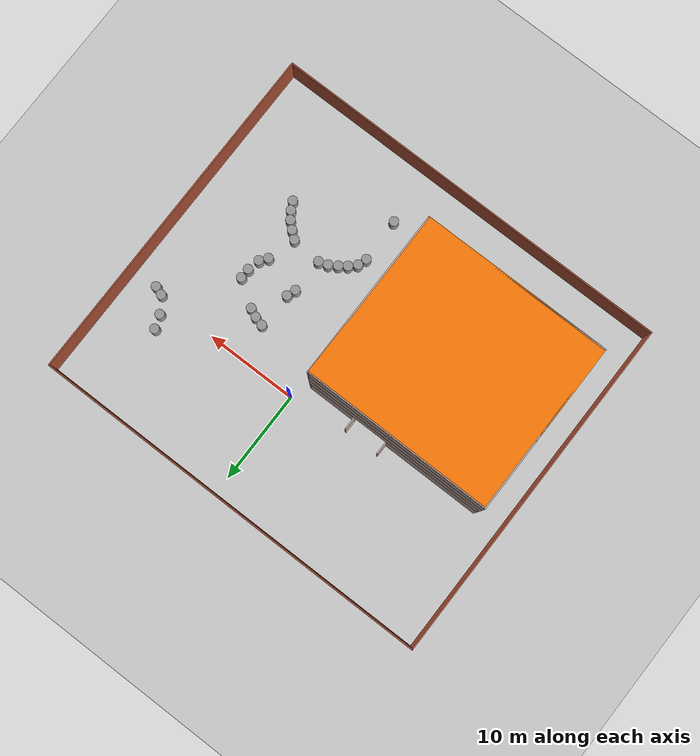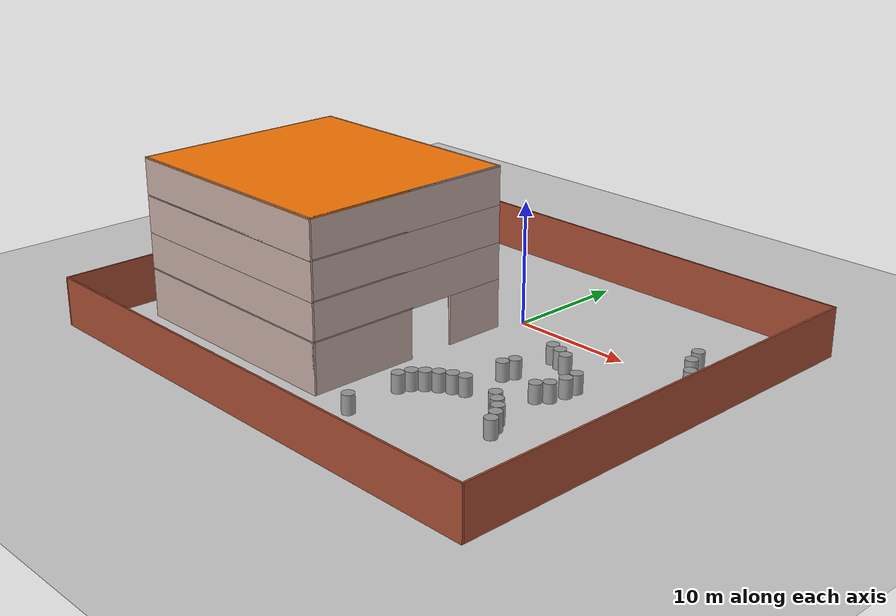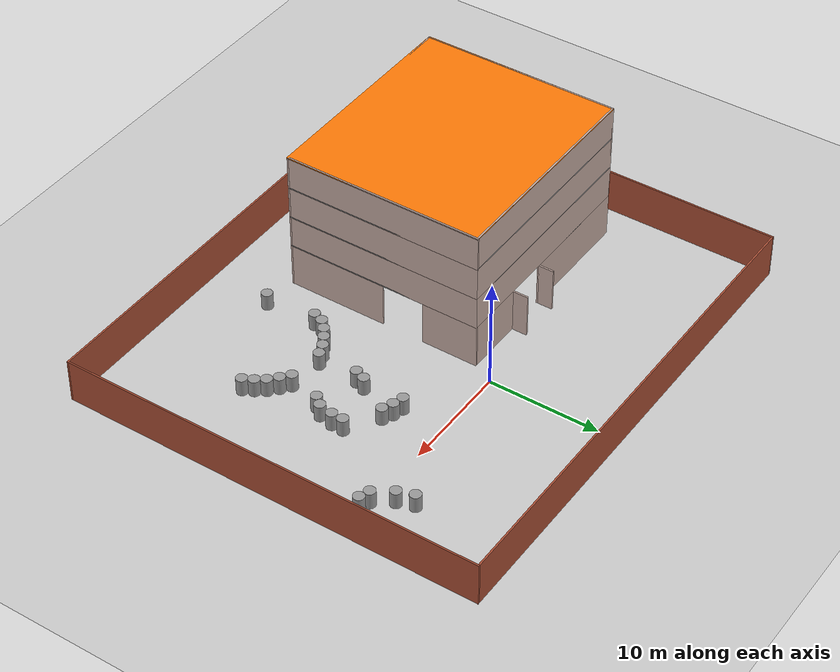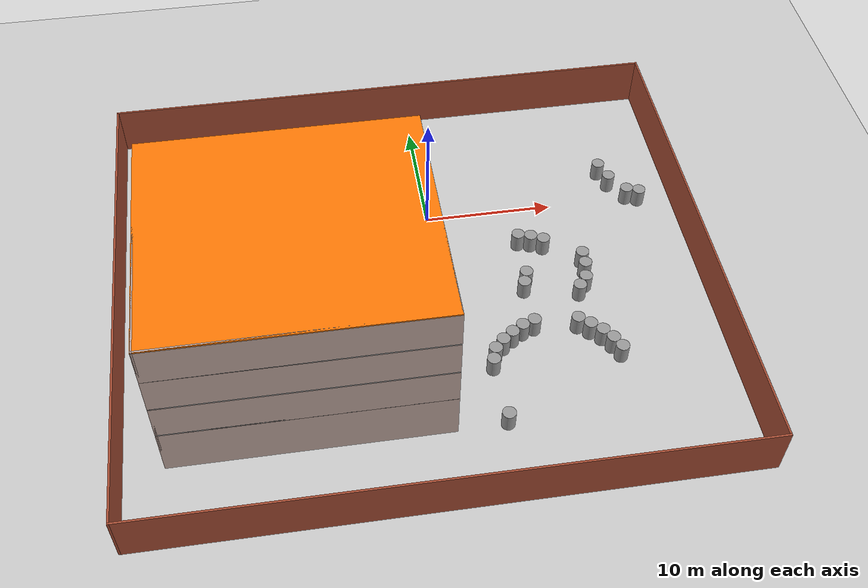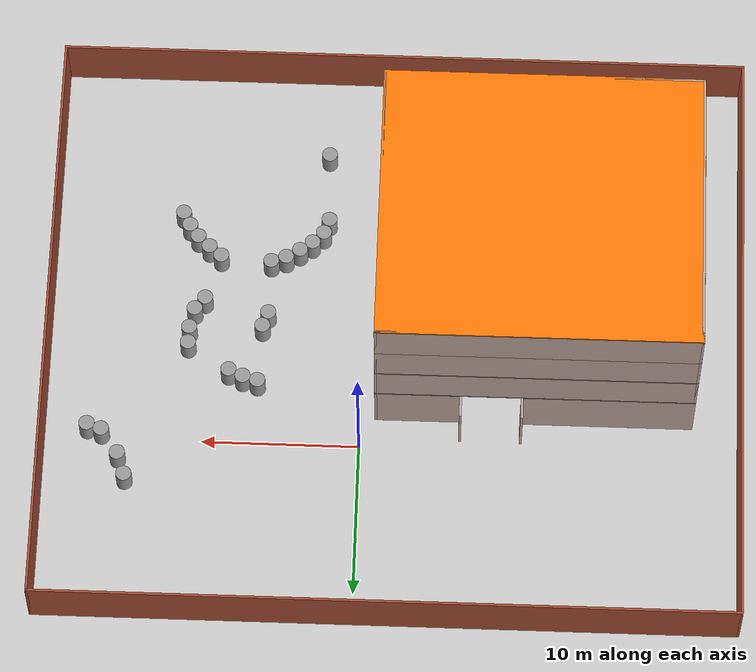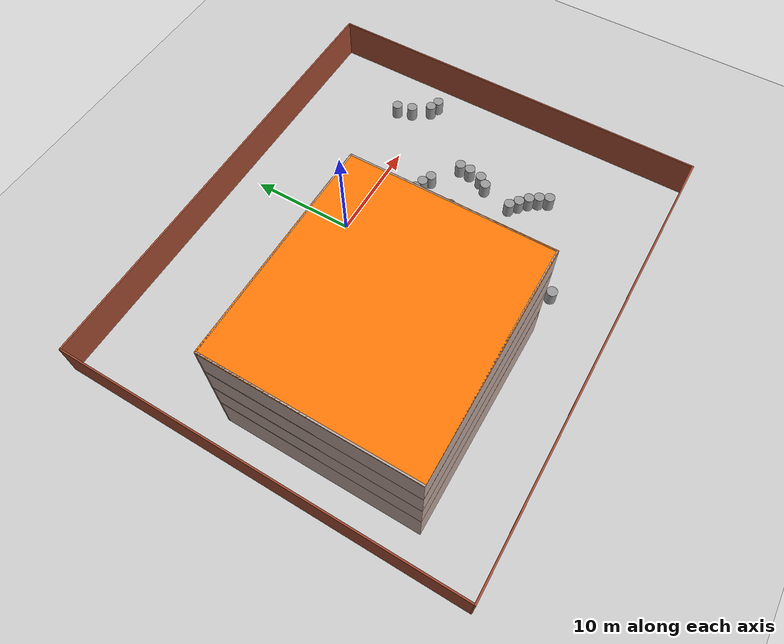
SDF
<sdf version="1.6">
 <world name="default">
  <light name="sun" type="directional">
   <pose>0 0 10 0 -0 0</pose>
   <diffuse>0.8 0.8 0.8 1</diffuse>
   <specular>0.2 0.2 0.2 1</specular>
   <attenuation>
    <range>1000</range>
    <constant>0.9</constant>
    <linear>0.01</linear>
    <quadratic>0.001</quadratic>
   </attenuation>
   <direction>-0.5 0.1 -0.9</direction>
  </light>
  <model name="ground_plane">
   <static>1</static>
   <link name="link">
    <collision name="collision">
     <geometry><plane><normal>0 0 1</normal><size>100 100</size></plane></geometry>
     <surface><friction><ode><mu>100</mu><mu2>50</mu2></ode></friction></surface>
    </collision>
    <visual name="visual">
     <cast_shadows>0</cast_shadows>
     <geometry><plane><normal>0 0 1</normal><size>100 100</size></plane></geometry>
     <material>
      <script><uri>file://media/materials/scripts/gazebo.material</uri><name>Gazebo/Grey</name></script>
     </material>
    </visual>
   </link>
  </model>
  <gravity>0 0 -9.8</gravity>
  <magnetic_field>6e-06 2.3e-05 -4.2e-05</magnetic_field>
  <atmosphere type="adiabatic"/>
  <physics name="default_physics" default="0" type="ode">
   <max_step_size>0.001</max_step_size>
   <real_time_factor>1</real_time_factor>
   <real_time_update_rate>1000</real_time_update_rate>
  </physics>
  <scene><ambient>0.4 0.4 0.4 1</ambient><background>0.7 0.7 0.7 1</background><shadows>1</shadows></scene>
  <audio><device>default</device></audio>
  <spherical_coordinates>
   <surface_model>EARTH_WGS84</surface_model>
   <latitude_deg>0</latitude_deg>
   <longitude_deg>0</longitude_deg>
   <elevation>0</elevation>
   <heading_deg>0</heading_deg>
  </spherical_coordinates>
  <model name="building2">
   <pose>-11 -10.325 0 0 -0 0</pose>
   <link name="Floor_0">
    <collision name="Floor_0_Collision">
     <geometry><box><size>20.15 18.15 0.1</size></box></geometry>
     <pose>0 0 0.05 0 -0 0</pose>
    </collision>
    <visual name="Floor_0_Visual">
     <pose>0 0 0.05 0 -0 0</pose>
     <geometry><box><size>20.15 18.15 0.1</size></box></geometry>
     <material>
      <script><uri>file://media/materials/scripts/gazebo.material</uri><name>Gazebo/Grey</name></script>
      <ambient>1 1 1 1</ambient>
     </material>
     <meta><layer>1</layer></meta>
    </visual>
    <pose>-0 -0.675 4 0 -0 0</pose>
   </link>
   <link name="Floor_2">
    <collision name="Floor_2_Collision">
     <geometry><box><size>20.15 18.15 0.1</size></box></geometry>
     <pose>0 0 0.05 0 -0 0</pose>
    </collision>
    <visual name="Floor_2_Visual">
     <pose>0 0 0.05 0 -0 0</pose>
     <geometry><box><size>20.15 18.15 0.1</size></box></geometry>
     <material>
      <script><uri>file://media/materials/scripts/gazebo.material</uri><name>Gazebo/Grey</name></script>
      <ambient>1 1 1 1</ambient>
     </material>
     <meta><layer>2</layer></meta>
    </visual>
    <pose>-0 -0.675 7 0 -0 0</pose>
   </link>
   <link name="Floor_3">
    <collision name="Floor_3_Collision">
     <geometry><box><size>20.15 18.15 0.1</size></box></geometry>
     <pose>0 0 0.05 0 -0 0</pose>
    </collision>
    <visual name="Floor_3_Visual">
     <pose>0 0 0.05 0 -0 0</pose>
     <geometry><box><size>20.15 18.15 0.1</size></box></geometry>
     <material>
      <script><uri>file://media/materials/scripts/gazebo.material</uri><name>Gazebo/Grey</name></script>
      <ambient>1 1 1 1</ambient>
     </material>
     <meta><layer>3</layer></meta>
    </visual>
    <pose>-0 -0.675 10 0 -0 0</pose>
   </link>
   <link name="Floor_8">
    <collision name="Floor_8_Collision">
     <geometry><box><size>20.15 18.15 0.1</size></box></geometry>
     <pose>0 0 0.05 0 -0 0</pose>
    </collision>
    <visual name="Floor_8_Visual">
     <pose>0 0 0.05 0 -0 0</pose>
     <geometry><box><size>20.15 18.15 0.1</size></box></geometry>
     <material>
      <script><uri>file://media/materials/scripts/gazebo.material</uri><name>Gazebo/Grey</name></script>
      <ambient>0.996078 0.47451 0.0196078 1</ambient>
     </material>
     <meta><layer>4</layer></meta>
    </visual>
    <pose>-0 -0.675 13 0 -0 0</pose>
   </link>
   <link name="Wall_11">
    <collision name="Wall_11_Collision">
     <geometry><box><size>1.5 0.15 4</size></box></geometry>
     <pose>0 0 2 0 -0 0</pose>
    </collision>
    <visual name="Wall_11_Visual">
     <pose>0 0 2 0 -0 0</pose>
     <geometry><box><size>1.5 0.15 4</size></box></geometry>
     <material>
      <script><uri>file://media/materials/scripts/gazebo.material</uri><name>Gazebo/Grey</name></script>
      <ambient>0.760784 0.662745 0.627451 1</ambient>
     </material>
     <meta><layer>0</layer></meta>
    </visual>
    <pose>0.8 9 0 0 -0 -1.5708</pose>
   </link>
   <link name="Wall_12">
    <collision name="Wall_12_Collision">
     <geometry><box><size>10.95 0.15 4</size></box></geometry>
     <pose>0 0 2 0 -0 0</pose>
    </collision>
    <visual name="Wall_12_Visual">
     <pose>0 0 2 0 -0 0</pose>
     <geometry><box><size>10.95 0.15 4</size></box></geometry>
     <material>
      <script><uri>file://media/materials/scripts/gazebo.material</uri><name>Gazebo/Grey</name></script>
      <ambient>0.760784 0.662745 0.627451 1</ambient>
     </material>
     <meta><layer>0</layer></meta>
    </visual>
    <pose>-4.6 8.325 0 0 -0 3.14159</pose>
   </link>
   <link name="Wall_14">
    <collision name="Wall_14_Collision">
     <geometry><box><size>18.15 0.15 4</size></box></geometry>
     <pose>0 0 2 0 -0 0</pose>
    </collision>
    <visual name="Wall_14_Visual">
     <pose>0 0 2 0 -0 0</pose>
     <geometry><box><size>18.15 0.15 4</size></box></geometry>
     <material>
      <script><uri>file://media/materials/scripts/gazebo.material</uri><name>Gazebo/Grey</name></script>
      <ambient>0.760784 0.662745 0.627451 1</ambient>
     </material>
     <meta><layer>0</layer></meta>
    </visual>
    <pose>-10 -0.675 0 0 -0 -1.5708</pose>
   </link>
   <link name="Wall_16">
    <collision name="Wall_16_Collision">
     <geometry><box><size>20.15 0.15 4</size></box></geometry>
     <pose>0 0 2 0 -0 0</pose>
    </collision>
    <visual name="Wall_16_Visual">
     <pose>0 0 2 0 -0 0</pose>
     <geometry><box><size>20.15 0.15 4</size></box></geometry>
     <material>
      <script><uri>file://media/materials/scripts/gazebo.material</uri><name>Gazebo/Grey</name></script>
      <ambient>0.760784 0.662745 0.627451 1</ambient>
     </material>
     <meta><layer>0</layer></meta>
    </visual>
    <pose>-0 -9.675 0 0 -0 0</pose>
   </link>
   <link name="Wall_24">
    <collision name="Wall_24_Collision">
     <geometry><box><size>18.15 0.15 3</size></box></geometry>
     <pose>0 0 1.5 0 -0 0</pose>
    </collision>
    <visual name="Wall_24_Visual">
     <pose>0 0 1.5 0 -0 0</pose>
     <geometry><box><size>18.15 0.15 3</size></box></geometry>
     <material>
      <script><uri>file://media/materials/scripts/gazebo.material</uri><name>Gazebo/Grey</name></script>
      <ambient>0.760784 0.662745 0.627451 1</ambient>
     </material>
     <meta><layer>1</layer></meta>
    </visual>
    <pose>-10 -0.675 4 0 -0 -1.5708</pose>
   </link>
   <link name="Wall_25">
    <collision name="Wall_25_Collision">
     <geometry><box><size>20.15 0.15 3</size></box></geometry>
     <pose>0 0 1.5 0 -0 0</pose>
    </collision>
    <visual name="Wall_25_Visual">
     <pose>0 0 1.5 0 -0 0</pose>
     <geometry><box><size>20.15 0.15 3</size></box></geometry>
     <material>
      <script><uri>file://media/materials/scripts/gazebo.material</uri><name>Gazebo/Grey</name></script>
      <ambient>0.760784 0.662745 0.627451 1</ambient>
     </material>
     <meta><layer>1</layer></meta>
    </visual>
    <pose>-0 -9.675 4 0 -0 0</pose>
   </link>
   <link name="Wall_31">
    <collision name="Wall_31_Collision">
     <geometry><box><size>20.15 0.15 3</size></box></geometry>
     <pose>0 0 1.5 0 -0 0</pose>
    </collision>
    <visual name="Wall_31_Visual">
     <pose>0 0 1.5 0 -0 0</pose>
     <geometry><box><size>20.15 0.15 3</size></box></geometry>
     <material>
      <script><uri>file://media/materials/scripts/gazebo.material</uri><name>Gazebo/Grey</name></script>
      <ambient>0.760784 0.662745 0.627451 1</ambient>
     </material>
     <meta><layer>1</layer></meta>
    </visual>
    <pose>-0 8.325 4 0 -0 0</pose>
   </link>
   <link name="Wall_33">
    <collision name="Wall_33_Collision">
     <geometry><box><size>18 0.15 3</size></box></geometry>
     <pose>0 0 1.5 0 -0 0</pose>
    </collision>
    <visual name="Wall_33_Visual">
     <pose>0 0 1.5 0 -0 0</pose>
     <geometry><box><size>18 0.15 3</size></box></geometry>
     <material>
      <script><uri>file://media/materials/scripts/gazebo.material</uri><name>Gazebo/Grey</name></script>
      <ambient>0.760784 0.662745 0.627451 1</ambient>
     </material>
     <meta><layer>1</layer></meta>
    </visual>
    <pose>10 -0.6 4 0 -0 -1.5708</pose>
   </link>
   <link name="Wall_4">
    <collision name="Wall_4_Collision">
     <geometry><box><size>5.15 0.15 4</size></box></geometry>
     <pose>0 0 2 0 -0 0</pose>
    </collision>
    <visual name="Wall_4_Visual">
     <pose>0 0 2 0 -0 0</pose>
     <geometry><box><size>5.15 0.15 4</size></box></geometry>
     <material>
      <script><uri>file://media/materials/scripts/gazebo.material</uri><name>Gazebo/Grey</name></script>
      <ambient>0.760784 0.662745 0.627451 1</ambient>
     </material>
     <meta><layer>0</layer></meta>
    </visual>
    <pose>10 5.825 0 0 -0 -1.5708</pose>
   </link>
   <link name="Wall_42">
    <collision name="Wall_42_Collision">
     <geometry><box><size>18.15 0.15 3</size></box></geometry>
     <pose>0 0 1.5 0 -0 0</pose>
    </collision>
    <visual name="Wall_42_Visual">
     <pose>0 0 1.5 0 -0 0</pose>
     <geometry><box><size>18.15 0.15 3</size></box></geometry>
     <material>
      <script><uri>file://media/materials/scripts/gazebo.material</uri><name>Gazebo/Grey</name></script>
      <ambient>0.760784 0.662745 0.627451 1</ambient>
     </material>
     <meta><layer>2</layer></meta>
    </visual>
    <pose>-10 -0.675 7 0 -0 -1.5708</pose>
   </link>
   <link name="Wall_43">
    <collision name="Wall_43_Collision">
     <geometry><box><size>20.15 0.15 3</size></box></geometry>
     <pose>0 0 1.5 0 -0 0</pose>
    </collision>
    <visual name="Wall_43_Visual">
     <pose>0 0 1.5 0 -0 0</pose>
     <geometry><box><size>20.15 0.15 3</size></box></geometry>
     <material>
      <script><uri>file://media/materials/scripts/gazebo.material</uri><name>Gazebo/Grey</name></script>
      <ambient>0.760784 0.662745 0.627451 1</ambient>
     </material>
     <meta><layer>2</layer></meta>
    </visual>
    <pose>-0 -9.675 7 0 -0 0</pose>
   </link>
   <link name="Wall_44">
    <collision name="Wall_44_Collision">
     <geometry><box><size>20.15 0.15 3</size></box></geometry>
     <pose>0 0 1.5 0 -0 0</pose>
    </collision>
    <visual name="Wall_44_Visual">
     <pose>0 0 1.5 0 -0 0</pose>
     <geometry><box><size>20.15 0.15 3</size></box></geometry>
     <material>
      <script><uri>file://media/materials/scripts/gazebo.material</uri><name>Gazebo/Grey</name></script>
      <ambient>0.760784 0.662745 0.627451 1</ambient>
     </material>
     <meta><layer>2</layer></meta>
    </visual>
    <pose>-0 8.325 7 0 -0 0</pose>
   </link>
   <link name="Wall_45">
    <collision name="Wall_45_Collision">
     <geometry><box><size>18 0.15 3</size></box></geometry>
     <pose>0 0 1.5 0 -0 0</pose>
    </collision>
    <visual name="Wall_45_Visual">
     <pose>0 0 1.5 0 -0 0</pose>
     <geometry><box><size>18 0.15 3</size></box></geometry>
     <material>
      <script><uri>file://media/materials/scripts/gazebo.material</uri><name>Gazebo/Grey</name></script>
      <ambient>0.760784 0.662745 0.627451 1</ambient>
     </material>
     <meta><layer>2</layer></meta>
    </visual>
    <pose>10 -0.6 7 0 -0 -1.5708</pose>
   </link>
   <link name="Wall_46">
    <collision name="Wall_46_Collision">
     <geometry><box><size>18.15 0.15 3</size></box></geometry>
     <pose>0 0 1.5 0 -0 0</pose>
    </collision>
    <visual name="Wall_46_Visual">
     <pose>0 0 1.5 0 -0 0</pose>
     <geometry><box><size>18.15 0.15 3</size></box></geometry>
     <material>
      <script><uri>file://media/materials/scripts/gazebo.material</uri><name>Gazebo/Grey</name></script>
      <ambient>0.760784 0.662745 0.627451 1</ambient>
     </material>
     <meta><layer>3</layer></meta>
    </visual>
    <pose>-10 -0.675 10 0 -0 -1.5708</pose>
   </link>
   <link name="Wall_47">
    <collision name="Wall_47_Collision">
     <geometry><box><size>20.15 0.15 3</size></box></geometry>
     <pose>0 0 1.5 0 -0 0</pose>
    </collision>
    <visual name="Wall_47_Visual">
     <pose>0 0 1.5 0 -0 0</pose>
     <geometry><box><size>20.15 0.15 3</size></box></geometry>
     <material>
      <script><uri>file://media/materials/scripts/gazebo.material</uri><name>Gazebo/Grey</name></script>
      <ambient>0.760784 0.662745 0.627451 1</ambient>
     </material>
     <meta><layer>3</layer></meta>
    </visual>
    <pose>-0 -9.675 10 0 -0 0</pose>
   </link>
   <link name="Wall_48">
    <collision name="Wall_48_Collision">
     <geometry><box><size>20.15 0.15 3</size></box></geometry>
     <pose>0 0 1.5 0 -0 0</pose>
    </collision>
    <visual name="Wall_48_Visual">
     <pose>0 0 1.5 0 -0 0</pose>
     <geometry><box><size>20.15 0.15 3</size></box></geometry>
     <material>
      <script><uri>file://media/materials/scripts/gazebo.material</uri><name>Gazebo/Grey</name></script>
      <ambient>0.760784 0.662745 0.627451 1</ambient>
     </material>
     <meta><layer>3</layer></meta>
    </visual>
    <pose>-0 8.325 10 0 -0 0</pose>
   </link>
   <link name="Wall_49">
    <collision name="Wall_49_Collision">
     <geometry><box><size>18 0.15 3</size></box></geometry>
     <pose>0 0 1.5 0 -0 0</pose>
    </collision>
    <visual name="Wall_49_Visual">
     <pose>0 0 1.5 0 -0 0</pose>
     <geometry><box><size>18 0.15 3</size></box></geometry>
     <material>
      <script><uri>file://media/materials/scripts/gazebo.material</uri><name>Gazebo/Grey</name></script>
      <ambient>0.760784 0.662745 0.627451 1</ambient>
     </material>
     <meta><layer>3</layer></meta>
    </visual>
    <pose>10 -0.6 10 0 -0 -1.5708</pose>
   </link>
   <link name="Wall_6">
    <collision name="Wall_6_Collision">
     <geometry><box><size>9.15 0.15 4</size></box></geometry>
     <pose>0 0 2 0 -0 0</pose>
    </collision>
    <visual name="Wall_6_Visual">
     <pose>0 0 2 0 -0 0</pose>
     <geometry><box><size>9.15 0.15 4</size></box></geometry>
     <material>
      <script><uri>file://media/materials/scripts/gazebo.material</uri><name>Gazebo/Grey</name></script>
      <ambient>0.760784 0.662745 0.627451 1</ambient>
     </material>
     <meta><layer>0</layer></meta>
    </visual>
    <pose>10 -5.175 0 0 -0 -1.5708</pose>
   </link>
   <link name="Wall_76">
    <collision name="Wall_76_Collision">
     <geometry><box><size>18.15 0.15 0.1</size></box></geometry>
     <pose>0 0 0.05 0 -0 0</pose>
    </collision>
    <visual name="Wall_76_Visual">
     <pose>0 0 0.05 0 -0 0</pose>
     <geometry><box><size>18.15 0.15 0.1</size></box></geometry>
     <material>
      <script><uri>file://media/materials/scripts/gazebo.material</uri><name>Gazebo/Grey</name></script>
      <ambient>0.760784 0.662745 0.627451 1</ambient>
     </material>
     <meta><layer>4</layer></meta>
    </visual>
    <pose>-10 -0.675 13 0 -0 -1.5708</pose>
   </link>
   <link name="Wall_77">
    <collision name="Wall_77_Collision">
     <geometry><box><size>20.15 0.15 0.1</size></box></geometry>
     <pose>0 0 0.05 0 -0 0</pose>
    </collision>
    <visual name="Wall_77_Visual">
     <pose>0 0 0.05 0 -0 0</pose>
     <geometry><box><size>20.15 0.15 0.1</size></box></geometry>
     <material>
      <script><uri>file://media/materials/scripts/gazebo.material</uri><name>Gazebo/Grey</name></script>
      <ambient>0.760784 0.662745 0.627451 1</ambient>
     </material>
     <meta><layer>4</layer></meta>
    </visual>
    <pose>-0 -9.675 13 0 -0 0</pose>
   </link>
   <link name="Wall_78">
    <collision name="Wall_78_Collision">
     <geometry><box><size>20.15 0.15 0.1</size></box></geometry>
     <pose>0 0 0.05 0 -0 0</pose>
    </collision>
    <visual name="Wall_78_Visual">
     <pose>0 0 0.05 0 -0 0</pose>
     <geometry><box><size>20.15 0.15 0.1</size></box></geometry>
     <material>
      <script><uri>file://media/materials/scripts/gazebo.material</uri><name>Gazebo/Grey</name></script>
      <ambient>0.760784 0.662745 0.627451 1</ambient>
     </material>
     <meta><layer>4</layer></meta>
    </visual>
    <pose>-0 8.325 13 0 -0 0</pose>
   </link>
   <link name="Wall_79">
    <collision name="Wall_79_Collision">
     <geometry><box><size>18 0.15 0.1</size></box></geometry>
     <pose>0 0 0.05 0 -0 0</pose>
    </collision>
    <visual name="Wall_79_Visual">
     <pose>0 0 0.05 0 -0 0</pose>
     <geometry><box><size>18 0.15 0.1</size></box></geometry>
     <material>
      <script><uri>file://media/materials/scripts/gazebo.material</uri><name>Gazebo/Grey</name></script>
      <ambient>0.760784 0.662745 0.627451 1</ambient>
     </material>
     <meta><layer>4</layer></meta>
    </visual>
    <pose>10 -0.6 13 0 -0 -1.5708</pose>
   </link>
   <link name="Wall_8">
    <collision name="Wall_8_Collision">
     <geometry><box><size>5.5 0.15 4</size></box></geometry>
     <pose>0 0 2 0 -0 0</pose>
    </collision>
    <visual name="Wall_8_Visual">
     <pose>0 0 2 0 -0 0</pose>
     <geometry><box><size>5.5 0.15 4</size></box></geometry>
     <material>
      <script><uri>file://media/materials/scripts/gazebo.material</uri><name>Gazebo/Grey</name></script>
      <ambient>0.760784 0.662745 0.627451 1</ambient>
     </material>
     <meta><layer>0</layer></meta>
    </visual>
    <pose>7.325 8.325 0 0 -0 3.14159</pose>
   </link>
   <link name="Wall_9">
    <collision name="Wall_9_Collision">
     <geometry><box><size>1.5 0.15 4</size></box></geometry>
     <pose>0 0 2 0 -0 0</pose>
    </collision>
    <visual name="Wall_9_Visual">
     <pose>0 0 2 0 -0 0</pose>
     <geometry><box><size>1.5 0.15 4</size></box></geometry>
     <material>
      <script><uri>file://media/materials/scripts/gazebo.material</uri><name>Gazebo/Grey</name></script>
      <ambient>0.760784 0.662745 0.627451 1</ambient>
     </material>
     <meta><layer>0</layer></meta>
    </visual>
    <pose>4.65 9 0 0 -0 1.5708</pose>
   </link>
   <static>1</static>
  </model>
  <model name="wall11">
   <pose>-2 -7 0 0 -0 0</pose>
   <link name="Wall_0">
    <collision name="Wall_0_Collision">
     <geometry><box><size>44.15 0.15 4</size></box></geometry>
     <pose>0 0 2 0 -0 0</pose>
    </collision>
    <visual name="Wall_0_Visual">
     <pose>0 0 2 0 -0 0</pose>
     <geometry><box><size>44.15 0.15 4</size></box></geometry>
     <material>
      <script><uri>file://media/materials/scripts/gazebo.material</uri><name>Gazebo/Bricks</name></script>
      <ambient>1 1 1 1</ambient>
     </material>
     <meta><layer>0</layer></meta>
    </visual>
    <pose>0 19 0 0 -0 0</pose>
   </link>
   <link name="Wall_2">
    <collision name="Wall_2_Collision">
     <geometry><box><size>38.15 0.15 4</size></box></geometry>
     <pose>0 0 2 0 -0 0</pose>
    </collision>
    <visual name="Wall_2_Visual">
     <pose>0 0 2 0 -0 0</pose>
     <geometry><box><size>38.15 0.15 4</size></box></geometry>
     <material>
      <script><uri>file://media/materials/scripts/gazebo.material</uri><name>Gazebo/Bricks</name></script>
      <ambient>1 1 1 1</ambient>
     </material>
     <meta><layer>0</layer></meta>
    </visual>
    <pose>22 0 0 0 -0 -1.5708</pose>
   </link>
   <link name="Wall_4">
    <collision name="Wall_4_Collision">
     <geometry><box><size>44.15 0.15 4</size></box></geometry>
     <pose>0 0 2 0 -0 0</pose>
    </collision>
    <visual name="Wall_4_Visual">
     <pose>0 0 2 0 -0 0</pose>
     <geometry><box><size>44.15 0.15 4</size></box></geometry>
     <material>
      <script><uri>file://media/materials/scripts/gazebo.material</uri><name>Gazebo/Bricks</name></script>
      <ambient>1 1 1 1</ambient>
     </material>
     <meta><layer>0</layer></meta>
    </visual>
    <pose>0 -19 0 0 -0 3.14159</pose>
   </link>
   <link name="Wall_6">
    <collision name="Wall_6_Collision">
     <geometry><box><size>38.15 0.15 4</size></box></geometry>
     <pose>0 0 2 0 -0 0</pose>
    </collision>
    <visual name="Wall_6_Visual">
     <pose>0 0 2 0 -0 0</pose>
     <geometry><box><size>38.15 0.15 4</size></box></geometry>
     <material>
      <script><uri>file://media/materials/scripts/gazebo.material</uri><name>Gazebo/Bricks</name></script>
      <ambient>1 1 1 1</ambient>
     </material>
     <meta><layer>0</layer></meta>
    </visual>
    <pose>-22 0 0 0 -0 1.5708</pose>
   </link>
   <static>1</static>
  </model>
  <model name="cylinder1.5m">
   <link name="link">
    <inertial>
     <mass>1</mass>
     <inertia><ixx>0.145833</ixx><ixy>0</ixy><ixz>0</ixz><iyy>0.145833</iyy><iyz>0</iyz><izz>0.125</izz></inertia>
    </inertial>
    <pose>0 0 0.25 0 -0 0</pose>
    <visual name="visual">
     <geometry><cylinder><radius>0.5</radius><length>1.5</length></cylinder></geometry>
     <material>
      <script><name>Gazebo/Grey</name><uri>file://media/materials/scripts/gazebo.material</uri></script>
      <shader type="pixel"><normal_map>__default__</normal_map></shader>
      <ambient>0.3 0.3 0.3 1</ambient>
      <diffuse>0.7 0.7 0.7 1</diffuse>
      <specular>0.01 0.01 0.01 1</specular>
      <emissive>0 0 0 1</emissive>
     </material>
    </visual>
    <collision name="collision">
     <geometry><cylinder><radius>0.5</radius><length>1</length></cylinder></geometry>
     <surface>
      <friction>
       <ode><mu>1</mu><mu2>1</mu2><fdir1>0 0 0</fdir1><slip1>0</slip1><slip2>0</slip2></ode>
       <torsional>
        <coefficient>1</coefficient>
        <patch_radius>0</patch_radius>
        <surface_radius>0</surface_radius>
        <use_patch_radius>1</use_patch_radius>
        <ode><slip>0</slip></ode>
       </torsional>
      </friction>
      <bounce><restitution_coefficient>0</restitution_coefficient><threshold>1e+06</threshold></bounce>
      <contact>
       <collide_without_contact>0</collide_without_contact>
       <collide_without_contact_bitmask>1</collide_without_contact_bitmask>
       <collide_bitmask>1</collide_bitmask>
       <ode>
        <soft_cfm>0</soft_cfm>
        <soft_erp>0.2</soft_erp>
        <kp>1e+13</kp>
        <kd>1</kd>
        <max_vel>0.01</max_vel>
        <min_depth>0</min_depth>
       </ode>
       <bullet>
        <split_impulse>1</split_impulse>
        <split_impulse_penetration_threshold>-0.01</split_impulse_penetration_threshold>
        <soft_cfm>0</soft_cfm>
        <soft_erp>0.2</soft_erp>
        <kp>1e+13</kp>
        <kd>1</kd>
       </bullet>
      </contact>
     </surface>
    </collision>
   </link>
   <static>0</static>
   <pose>2.61988 -20 0.5 0 -0 0</pose>
  </model>
  <model name="cylinder1.5m_clone">
   <link name="link">
    <inertial>
     <mass>1</mass>
     <inertia><ixx>0.145833</ixx><ixy>0</ixy><ixz>0</ixz><iyy>0.145833</iyy><iyz>0</iyz><izz>0.125</izz></inertia>
    </inertial>
    <pose>0 0 0.25 0 -0 0</pose>
    <visual name="visual">
     <geometry><cylinder><radius>0.5</radius><length>1.5</length></cylinder></geometry>
     <material>
      <script><name>Gazebo/Grey</name><uri>file://media/materials/scripts/gazebo.material</uri></script>
      <shader type="pixel"><normal_map>__default__</normal_map></shader>
      <ambient>0.3 0.3 0.3 1</ambient>
      <diffuse>0.7 0.7 0.7 1</diffuse>
      <specular>0.01 0.01 0.01 1</specular>
      <emissive>0 0 0 1</emissive>
     </material>
    </visual>
    <collision name="collision">
     <geometry><cylinder><radius>0.5</radius><length>1</length></cylinder></geometry>
     <surface>
      <friction>
       <ode><mu>1</mu><mu2>1</mu2><fdir1>0 0 0</fdir1><slip1>0</slip1><slip2>0</slip2></ode>
       <torsional>
        <coefficient>1</coefficient>
        <patch_radius>0</patch_radius>
        <surface_radius>0</surface_radius>
        <use_patch_radius>1</use_patch_radius>
        <ode><slip>0</slip></ode>
       </torsional>
      </friction>
      <bounce><restitution_coefficient>0</restitution_coefficient><threshold>1e+06</threshold></bounce>
      <contact>
       <collide_without_contact>0</collide_without_contact>
       <collide_without_contact_bitmask>1</collide_without_contact_bitmask>
       <collide_bitmask>1</collide_bitmask>
       <ode>
        <soft_cfm>0</soft_cfm>
        <soft_erp>0.2</soft_erp>
        <kp>1e+13</kp>
        <kd>1</kd>
        <max_vel>0.01</max_vel>
        <min_depth>0</min_depth>
       </ode>
       <bullet>
        <split_impulse>1</split_impulse>
        <split_impulse_penetration_threshold>-0.01</split_impulse_penetration_threshold>
        <soft_cfm>0</soft_cfm>
        <soft_erp>0.2</soft_erp>
        <kp>1e+13</kp>
        <kd>1</kd>
       </bullet>
      </contact>
     </surface>
    </collision>
   </link>
   <static>0</static>
   <pose>10.1837 -9.48569 0.5 0 -0 0</pose>
  </model>
  <model name="cylinder1.5m_clone_0">
   <link name="link">
    <inertial>
     <mass>1</mass>
     <inertia><ixx>0.145833</ixx><ixy>0</ixy><ixz>0</ixz><iyy>0.145833</iyy><iyz>0</iyz><izz>0.125</izz></inertia>
    </inertial>
    <pose>0 0 0.25 0 -0 0</pose>
    <visual name="visual">
     <geometry><cylinder><radius>0.5</radius><length>1.5</length></cylinder></geometry>
     <material>
      <script><name>Gazebo/Grey</name><uri>file://media/materials/scripts/gazebo.material</uri></script>
      <shader type="pixel"><normal_map>__default__</normal_map></shader>
      <ambient>0.3 0.3 0.3 1</ambient>
      <diffuse>0.7 0.7 0.7 1</diffuse>
      <specular>0.01 0.01 0.01 1</specular>
      <emissive>0 0 0 1</emissive>
     </material>
    </visual>
    <collision name="collision">
     <geometry><cylinder><radius>0.5</radius><length>1</length></cylinder></geometry>
     <surface>
      <friction>
       <ode><mu>1</mu><mu2>1</mu2><fdir1>0 0 0</fdir1><slip1>0</slip1><slip2>0</slip2></ode>
       <torsional>
        <coefficient>1</coefficient>
        <patch_radius>0</patch_radius>
        <surface_radius>0</surface_radius>
        <use_patch_radius>1</use_patch_radius>
        <ode><slip>0</slip></ode>
       </torsional>
      </friction>
      <bounce><restitution_coefficient>0</restitution_coefficient><threshold>1e+06</threshold></bounce>
      <contact>
       <collide_without_contact>0</collide_without_contact>
       <collide_without_contact_bitmask>1</collide_without_contact_bitmask>
       <collide_bitmask>1</collide_bitmask>
       <ode>
        <soft_cfm>0</soft_cfm>
        <soft_erp>0.2</soft_erp>
        <kp>1e+13</kp>
        <kd>1</kd>
        <max_vel>0.01</max_vel>
        <min_depth>0</min_depth>
       </ode>
       <bullet>
        <split_impulse>1</split_impulse>
        <split_impulse_penetration_threshold>-0.01</split_impulse_penetration_threshold>
        <soft_cfm>0</soft_cfm>
        <soft_erp>0.2</soft_erp>
        <kp>1e+13</kp>
        <kd>1</kd>
       </bullet>
      </contact>
     </surface>
    </collision>
   </link>
   <static>0</static>
   <pose>10.8166 -8.69771 0.5 0 -0 0</pose>
  </model>
  <model name="cylinder1.5m_clone_1">
   <link name="link">
    <inertial>
     <mass>1</mass>
     <inertia><ixx>0.145833</ixx><ixy>0</ixy><ixz>0</ixz><iyy>0.145833</iyy><iyz>0</iyz><izz>0.125</izz></inertia>
    </inertial>
    <pose>0 0 0.25 0 -0 0</pose>
    <visual name="visual">
     <geometry><cylinder><radius>0.5</radius><length>1.5</length></cylinder></geometry>
     <material>
      <script><name>Gazebo/Grey</name><uri>file://media/materials/scripts/gazebo.material</uri></script>
      <shader type="pixel"><normal_map>__default__</normal_map></shader>
      <ambient>0.3 0.3 0.3 1</ambient>
      <diffuse>0.7 0.7 0.7 1</diffuse>
      <specular>0.01 0.01 0.01 1</specular>
      <emissive>0 0 0 1</emissive>
     </material>
    </visual>
    <collision name="collision">
     <geometry><cylinder><radius>0.5</radius><length>1</length></cylinder></geometry>
     <surface>
      <friction>
       <ode><mu>1</mu><mu2>1</mu2><fdir1>0 0 0</fdir1><slip1>0</slip1><slip2>0</slip2></ode>
       <torsional>
        <coefficient>1</coefficient>
        <patch_radius>0</patch_radius>
        <surface_radius>0</surface_radius>
        <use_patch_radius>1</use_patch_radius>
        <ode><slip>0</slip></ode>
       </torsional>
      </friction>
      <bounce><restitution_coefficient>0</restitution_coefficient><threshold>1e+06</threshold></bounce>
      <contact>
       <collide_without_contact>0</collide_without_contact>
       <collide_without_contact_bitmask>1</collide_without_contact_bitmask>
       <collide_bitmask>1</collide_bitmask>
       <ode>
        <soft_cfm>0</soft_cfm>
        <soft_erp>0.2</soft_erp>
        <kp>1e+13</kp>
        <kd>1</kd>
        <max_vel>0.01</max_vel>
        <min_depth>0</min_depth>
       </ode>
       <bullet>
        <split_impulse>1</split_impulse>
        <split_impulse_penetration_threshold>-0.01</split_impulse_penetration_threshold>
        <soft_cfm>0</soft_cfm>
        <soft_erp>0.2</soft_erp>
        <kp>1e+13</kp>
        <kd>1</kd>
       </bullet>
      </contact>
     </surface>
    </collision>
   </link>
   <static>0</static>
   <pose>11.0955 -7.37475 0.5 0 -0 0</pose>
  </model>
  <model name="cylinder1.5m_clone_2">
   <link name="link">
    <inertial>
     <mass>1</mass>
     <inertia><ixx>0.145833</ixx><ixy>0</ixy><ixz>0</ixz><iyy>0.145833</iyy><iyz>0</iyz><izz>0.125</izz></inertia>
    </inertial>
    <pose>0 0 0.25 0 -0 0</pose>
    <visual name="visual">
     <geometry><cylinder><radius>0.5</radius><length>1.5</length></cylinder></geometry>
     <material>
      <script><name>Gazebo/Grey</name><uri>file://media/materials/scripts/gazebo.material</uri></script>
      <shader type="pixel"><normal_map>__default__</normal_map></shader>
      <ambient>0.3 0.3 0.3 1</ambient>
      <diffuse>0.7 0.7 0.7 1</diffuse>
      <specular>0.01 0.01 0.01 1</specular>
      <emissive>0 0 0 1</emissive>
     </material>
    </visual>
    <collision name="collision">
     <geometry><cylinder><radius>0.5</radius><length>1</length></cylinder></geometry>
     <surface>
      <friction>
       <ode><mu>1</mu><mu2>1</mu2><fdir1>0 0 0</fdir1><slip1>0</slip1><slip2>0</slip2></ode>
       <torsional>
        <coefficient>1</coefficient>
        <patch_radius>0</patch_radius>
        <surface_radius>0</surface_radius>
        <use_patch_radius>1</use_patch_radius>
        <ode><slip>0</slip></ode>
       </torsional>
      </friction>
      <bounce><restitution_coefficient>0</restitution_coefficient><threshold>1e+06</threshold></bounce>
      <contact>
       <collide_without_contact>0</collide_without_contact>
       <collide_without_contact_bitmask>1</collide_without_contact_bitmask>
       <collide_bitmask>1</collide_bitmask>
       <ode>
        <soft_cfm>0</soft_cfm>
        <soft_erp>0.2</soft_erp>
        <kp>1e+13</kp>
        <kd>1</kd>
        <max_vel>0.01</max_vel>
        <min_depth>0</min_depth>
       </ode>
       <bullet>
        <split_impulse>1</split_impulse>
        <split_impulse_penetration_threshold>-0.01</split_impulse_penetration_threshold>
        <soft_cfm>0</soft_cfm>
        <soft_erp>0.2</soft_erp>
        <kp>1e+13</kp>
        <kd>1</kd>
       </bullet>
      </contact>
     </surface>
    </collision>
   </link>
   <static>0</static>
   <pose>11.119 -6.30171 0.5 0 -0 0</pose>
  </model>
  <model name="cylinder1.5m_clone_3">
   <link name="link">
    <inertial>
     <mass>1</mass>
     <inertia><ixx>0.145833</ixx><ixy>0</ixy><ixz>0</ixz><iyy>0.145833</iyy><iyz>0</iyz><izz>0.125</izz></inertia>
    </inertial>
    <pose>0 0 0.25 0 -0 0</pose>
    <visual name="visual">
     <geometry><cylinder><radius>0.5</radius><length>1.5</length></cylinder></geometry>
     <material>
      <script><name>Gazebo/Grey</name><uri>file://media/materials/scripts/gazebo.material</uri></script>
      <shader type="pixel"><normal_map>__default__</normal_map></shader>
      <ambient>0.3 0.3 0.3 1</ambient>
      <diffuse>0.7 0.7 0.7 1</diffuse>
      <specular>0.01 0.01 0.01 1</specular>
      <emissive>0 0 0 1</emissive>
     </material>
    </visual>
    <collision name="collision">
     <geometry><cylinder><radius>0.5</radius><length>1</length></cylinder></geometry>
     <surface>
      <friction>
       <ode><mu>1</mu><mu2>1</mu2><fdir1>0 0 0</fdir1><slip1>0</slip1><slip2>0</slip2></ode>
       <torsional>
        <coefficient>1</coefficient>
        <patch_radius>0</patch_radius>
        <surface_radius>0</surface_radius>
        <use_patch_radius>1</use_patch_radius>
        <ode><slip>0</slip></ode>
       </torsional>
      </friction>
      <bounce><restitution_coefficient>0</restitution_coefficient><threshold>1e+06</threshold></bounce>
      <contact>
       <collide_without_contact>0</collide_without_contact>
       <collide_without_contact_bitmask>1</collide_without_contact_bitmask>
       <collide_bitmask>1</collide_bitmask>
       <ode>
        <soft_cfm>0</soft_cfm>
        <soft_erp>0.2</soft_erp>
        <kp>1e+13</kp>
        <kd>1</kd>
        <max_vel>0.01</max_vel>
        <min_depth>0</min_depth>
       </ode>
       <bullet>
        <split_impulse>1</split_impulse>
        <split_impulse_penetration_threshold>-0.01</split_impulse_penetration_threshold>
        <soft_cfm>0</soft_cfm>
        <soft_erp>0.2</soft_erp>
        <kp>1e+13</kp>
        <kd>1</kd>
       </bullet>
      </contact>
     </surface>
    </collision>
   </link>
   <static>0</static>
   <pose>2.46274 -15.3169 0.5 0 -0 0</pose>
  </model>
  <model name="cylinder1.5m_clone_4">
   <link name="link">
    <inertial>
     <mass>1</mass>
     <inertia><ixx>0.145833</ixx><ixy>0</ixy><ixz>0</ixz><iyy>0.145833</iyy><iyz>0</iyz><izz>0.125</izz></inertia>
    </inertial>
    <pose>0 0 0.25 0 -0 0</pose>
    <visual name="visual">
     <geometry><cylinder><radius>0.5</radius><length>1.5</length></cylinder></geometry>
     <material>
      <script><name>Gazebo/Grey</name><uri>file://media/materials/scripts/gazebo.material</uri></script>
      <shader type="pixel"><normal_map>__default__</normal_map></shader>
      <ambient>0.3 0.3 0.3 1</ambient>
      <diffuse>0.7 0.7 0.7 1</diffuse>
      <specular>0.01 0.01 0.01 1</specular>
      <emissive>0 0 0 1</emissive>
     </material>
    </visual>
    <collision name="collision">
     <geometry><cylinder><radius>0.5</radius><length>1</length></cylinder></geometry>
     <surface>
      <friction>
       <ode><mu>1</mu><mu2>1</mu2><fdir1>0 0 0</fdir1><slip1>0</slip1><slip2>0</slip2></ode>
       <torsional>
        <coefficient>1</coefficient>
        <patch_radius>0</patch_radius>
        <surface_radius>0</surface_radius>
        <use_patch_radius>1</use_patch_radius>
        <ode><slip>0</slip></ode>
       </torsional>
      </friction>
      <bounce><restitution_coefficient>0</restitution_coefficient><threshold>1e+06</threshold></bounce>
      <contact>
       <collide_without_contact>0</collide_without_contact>
       <collide_without_contact_bitmask>1</collide_without_contact_bitmask>
       <collide_bitmask>1</collide_bitmask>
       <ode>
        <soft_cfm>0</soft_cfm>
        <soft_erp>0.2</soft_erp>
        <kp>1e+13</kp>
        <kd>1</kd>
        <max_vel>0.01</max_vel>
        <min_depth>0</min_depth>
       </ode>
       <bullet>
        <split_impulse>1</split_impulse>
        <split_impulse_penetration_threshold>-0.01</split_impulse_penetration_threshold>
        <soft_cfm>0</soft_cfm>
        <soft_erp>0.2</soft_erp>
        <kp>1e+13</kp>
        <kd>1</kd>
       </bullet>
      </contact>
     </surface>
    </collision>
   </link>
   <static>0</static>
   <pose>2.78004 -14.3644 0.5 0 -0 0</pose>
  </model>
  <model name="cylinder1.5m_clone_5">
   <link name="link">
    <inertial>
     <mass>1</mass>
     <inertia><ixx>0.145833</ixx><ixy>0</ixy><ixz>0</ixz><iyy>0.145833</iyy><iyz>0</iyz><izz>0.125</izz></inertia>
    </inertial>
    <pose>0 0 0.25 0 -0 0</pose>
    <visual name="visual">
     <geometry><cylinder><radius>0.5</radius><length>1.5</length></cylinder></geometry>
     <material>
      <script><name>Gazebo/Grey</name><uri>file://media/materials/scripts/gazebo.material</uri></script>
      <shader type="pixel"><normal_map>__default__</normal_map></shader>
      <ambient>0.3 0.3 0.3 1</ambient>
      <diffuse>0.7 0.7 0.7 1</diffuse>
      <specular>0.01 0.01 0.01 1</specular>
      <emissive>0 0 0 1</emissive>
     </material>
    </visual>
    <collision name="collision">
     <geometry><cylinder><radius>0.5</radius><length>1</length></cylinder></geometry>
     <surface>
      <friction>
       <ode><mu>1</mu><mu2>1</mu2><fdir1>0 0 0</fdir1><slip1>0</slip1><slip2>0</slip2></ode>
       <torsional>
        <coefficient>1</coefficient>
        <patch_radius>0</patch_radius>
        <surface_radius>0</surface_radius>
        <use_patch_radius>1</use_patch_radius>
        <ode><slip>0</slip></ode>
       </torsional>
      </friction>
      <bounce><restitution_coefficient>0</restitution_coefficient><threshold>1e+06</threshold></bounce>
      <contact>
       <collide_without_contact>0</collide_without_contact>
       <collide_without_contact_bitmask>1</collide_without_contact_bitmask>
       <collide_bitmask>1</collide_bitmask>
       <ode>
        <soft_cfm>0</soft_cfm>
        <soft_erp>0.2</soft_erp>
        <kp>1e+13</kp>
        <kd>1</kd>
        <max_vel>0.01</max_vel>
        <min_depth>0</min_depth>
       </ode>
       <bullet>
        <split_impulse>1</split_impulse>
        <split_impulse_penetration_threshold>-0.01</split_impulse_penetration_threshold>
        <soft_cfm>0</soft_cfm>
        <soft_erp>0.2</soft_erp>
        <kp>1e+13</kp>
        <kd>1</kd>
       </bullet>
      </contact>
     </surface>
    </collision>
   </link>
   <static>0</static>
   <pose>3.48146 -13.6596 0.5 0 -0 0</pose>
  </model>
  <model name="cylinder1.5m_clone_6">
   <link name="link">
    <inertial>
     <mass>1</mass>
     <inertia><ixx>0.145833</ixx><ixy>0</ixy><ixz>0</ixz><iyy>0.145833</iyy><iyz>0</iyz><izz>0.125</izz></inertia>
    </inertial>
    <pose>0 0 0.25 0 -0 0</pose>
    <visual name="visual">
     <geometry><cylinder><radius>0.5</radius><length>1.5</length></cylinder></geometry>
     <material>
      <script><name>Gazebo/Grey</name><uri>file://media/materials/scripts/gazebo.material</uri></script>
      <shader type="pixel"><normal_map>__default__</normal_map></shader>
      <ambient>0.3 0.3 0.3 1</ambient>
      <diffuse>0.7 0.7 0.7 1</diffuse>
      <specular>0.01 0.01 0.01 1</specular>
      <emissive>0 0 0 1</emissive>
     </material>
    </visual>
    <collision name="collision">
     <geometry><cylinder><radius>0.5</radius><length>1</length></cylinder></geometry>
     <surface>
      <friction>
       <ode><mu>1</mu><mu2>1</mu2><fdir1>0 0 0</fdir1><slip1>0</slip1><slip2>0</slip2></ode>
       <torsional>
        <coefficient>1</coefficient>
        <patch_radius>0</patch_radius>
        <surface_radius>0</surface_radius>
        <use_patch_radius>1</use_patch_radius>
        <ode><slip>0</slip></ode>
       </torsional>
      </friction>
      <bounce><restitution_coefficient>0</restitution_coefficient><threshold>1e+06</threshold></bounce>
      <contact>
       <collide_without_contact>0</collide_without_contact>
       <collide_without_contact_bitmask>1</collide_without_contact_bitmask>
       <collide_bitmask>1</collide_bitmask>
       <ode>
        <soft_cfm>0</soft_cfm>
        <soft_erp>0.2</soft_erp>
        <kp>1e+13</kp>
        <kd>1</kd>
        <max_vel>0.01</max_vel>
        <min_depth>0</min_depth>
       </ode>
       <bullet>
        <split_impulse>1</split_impulse>
        <split_impulse_penetration_threshold>-0.01</split_impulse_penetration_threshold>
        <soft_cfm>0</soft_cfm>
        <soft_erp>0.2</soft_erp>
        <kp>1e+13</kp>
        <kd>1</kd>
       </bullet>
      </contact>
     </surface>
    </collision>
   </link>
   <static>0</static>
   <pose>4.26908 -13.0841 0.5 0 -0 0</pose>
  </model>
  <model name="cylinder1.5m_clone_7">
   <link name="link">
    <inertial>
     <mass>1</mass>
     <inertia><ixx>0.145833</ixx><ixy>0</ixy><ixz>0</ixz><iyy>0.145833</iyy><iyz>0</iyz><izz>0.125</izz></inertia>
    </inertial>
    <pose>0 0 0.25 0 -0 0</pose>
    <visual name="visual">
     <geometry><cylinder><radius>0.5</radius><length>1.5</length></cylinder></geometry>
     <material>
      <script><name>Gazebo/Grey</name><uri>file://media/materials/scripts/gazebo.material</uri></script>
      <shader type="pixel"><normal_map>__default__</normal_map></shader>
      <ambient>0.3 0.3 0.3 1</ambient>
      <diffuse>0.7 0.7 0.7 1</diffuse>
      <specular>0.01 0.01 0.01 1</specular>
      <emissive>0 0 0 1</emissive>
     </material>
    </visual>
    <collision name="collision">
     <geometry><cylinder><radius>0.5</radius><length>1</length></cylinder></geometry>
     <surface>
      <friction>
       <ode><mu>1</mu><mu2>1</mu2><fdir1>0 0 0</fdir1><slip1>0</slip1><slip2>0</slip2></ode>
       <torsional>
        <coefficient>1</coefficient>
        <patch_radius>0</patch_radius>
        <surface_radius>0</surface_radius>
        <use_patch_radius>1</use_patch_radius>
        <ode><slip>0</slip></ode>
       </torsional>
      </friction>
      <bounce><restitution_coefficient>0</restitution_coefficient><threshold>1e+06</threshold></bounce>
      <contact>
       <collide_without_contact>0</collide_without_contact>
       <collide_without_contact_bitmask>1</collide_without_contact_bitmask>
       <collide_bitmask>1</collide_bitmask>
       <ode>
        <soft_cfm>0</soft_cfm>
        <soft_erp>0.2</soft_erp>
        <kp>1e+13</kp>
        <kd>1</kd>
        <max_vel>0.01</max_vel>
        <min_depth>0</min_depth>
       </ode>
       <bullet>
        <split_impulse>1</split_impulse>
        <split_impulse_penetration_threshold>-0.01</split_impulse_penetration_threshold>
        <soft_cfm>0</soft_cfm>
        <soft_erp>0.2</soft_erp>
        <kp>1e+13</kp>
        <kd>1</kd>
       </bullet>
      </contact>
     </surface>
    </collision>
   </link>
   <static>0</static>
   <pose>5.13352 -12.5607 0.5 0 -0 0</pose>
  </model>
  <model name="cylinder1.5m_clone_8">
   <link name="link">
    <inertial>
     <mass>1</mass>
     <inertia><ixx>0.145833</ixx><ixy>0</ixy><ixz>0</ixz><iyy>0.145833</iyy><iyz>0</iyz><izz>0.125</izz></inertia>
    </inertial>
    <pose>0 0 0.25 0 -0 0</pose>
    <visual name="visual">
     <geometry><cylinder><radius>0.5</radius><length>1.5</length></cylinder></geometry>
     <material>
      <script><name>Gazebo/Grey</name><uri>file://media/materials/scripts/gazebo.material</uri></script>
      <shader type="pixel"><normal_map>__default__</normal_map></shader>
      <ambient>0.3 0.3 0.3 1</ambient>
      <diffuse>0.7 0.7 0.7 1</diffuse>
      <specular>0.01 0.01 0.01 1</specular>
      <emissive>0 0 0 1</emissive>
     </material>
    </visual>
    <collision name="collision">
     <geometry><cylinder><radius>0.5</radius><length>1</length></cylinder></geometry>
     <surface>
      <friction>
       <ode><mu>1</mu><mu2>1</mu2><fdir1>0 0 0</fdir1><slip1>0</slip1><slip2>0</slip2></ode>
       <torsional>
        <coefficient>1</coefficient>
        <patch_radius>0</patch_radius>
        <surface_radius>0</surface_radius>
        <use_patch_radius>1</use_patch_radius>
        <ode><slip>0</slip></ode>
       </torsional>
      </friction>
      <bounce><restitution_coefficient>0</restitution_coefficient><threshold>1e+06</threshold></bounce>
      <contact>
       <collide_without_contact>0</collide_without_contact>
       <collide_without_contact_bitmask>1</collide_without_contact_bitmask>
       <collide_bitmask>1</collide_bitmask>
       <ode>
        <soft_cfm>0</soft_cfm>
        <soft_erp>0.2</soft_erp>
        <kp>1e+13</kp>
        <kd>1</kd>
        <max_vel>0.01</max_vel>
        <min_depth>0</min_depth>
       </ode>
       <bullet>
        <split_impulse>1</split_impulse>
        <split_impulse_penetration_threshold>-0.01</split_impulse_penetration_threshold>
        <soft_cfm>0</soft_cfm>
        <soft_erp>0.2</soft_erp>
        <kp>1e+13</kp>
        <kd>1</kd>
       </bullet>
      </contact>
     </surface>
    </collision>
   </link>
   <static>0</static>
   <pose>6.0765 -12.2332 0.5 0 -0 0</pose>
  </model>
  <model name="cylinder1.5m_clone_9">
   <link name="link">
    <inertial>
     <mass>1</mass>
     <inertia><ixx>0.145833</ixx><ixy>0</ixy><ixz>0</ixz><iyy>0.145833</iyy><iyz>0</iyz><izz>0.125</izz></inertia>
    </inertial>
    <pose>0 0 0.25 0 -0 0</pose>
    <visual name="visual">
     <geometry><cylinder><radius>0.5</radius><length>1.5</length></cylinder></geometry>
     <material>
      <script><name>Gazebo/Grey</name><uri>file://media/materials/scripts/gazebo.material</uri></script>
      <shader type="pixel"><normal_map>__default__</normal_map></shader>
      <ambient>0.3 0.3 0.3 1</ambient>
      <diffuse>0.7 0.7 0.7 1</diffuse>
      <specular>0.01 0.01 0.01 1</specular>
      <emissive>0 0 0 1</emissive>
     </material>
    </visual>
    <collision name="collision">
     <geometry><cylinder><radius>0.5</radius><length>1</length></cylinder></geometry>
     <surface>
      <friction>
       <ode><mu>1</mu><mu2>1</mu2><fdir1>0 0 0</fdir1><slip1>0</slip1><slip2>0</slip2></ode>
       <torsional>
        <coefficient>1</coefficient>
        <patch_radius>0</patch_radius>
        <surface_radius>0</surface_radius>
        <use_patch_radius>1</use_patch_radius>
        <ode><slip>0</slip></ode>
       </torsional>
      </friction>
      <bounce><restitution_coefficient>0</restitution_coefficient><threshold>1e+06</threshold></bounce>
      <contact>
       <collide_without_contact>0</collide_without_contact>
       <collide_without_contact_bitmask>1</collide_without_contact_bitmask>
       <collide_bitmask>1</collide_bitmask>
       <ode>
        <soft_cfm>0</soft_cfm>
        <soft_erp>0.2</soft_erp>
        <kp>1e+13</kp>
        <kd>1</kd>
        <max_vel>0.01</max_vel>
        <min_depth>0</min_depth>
       </ode>
       <bullet>
        <split_impulse>1</split_impulse>
        <split_impulse_penetration_threshold>-0.01</split_impulse_penetration_threshold>
        <soft_cfm>0</soft_cfm>
        <soft_erp>0.2</soft_erp>
        <kp>1e+13</kp>
        <kd>1</kd>
       </bullet>
      </contact>
     </surface>
    </collision>
   </link>
   <static>0</static>
   <pose>9.30865 -12.508 0.5 0 -0 0</pose>
  </model>
  <model name="cylinder1.5m_clone_10">
   <link name="link">
    <inertial>
     <mass>1</mass>
     <inertia><ixx>0.145833</ixx><ixy>0</ixy><ixz>0</ixz><iyy>0.145833</iyy><iyz>0</iyz><izz>0.125</izz></inertia>
    </inertial>
    <pose>0 0 0.25 0 -0 0</pose>
    <visual name="visual">
     <geometry><cylinder><radius>0.5</radius><length>1.5</length></cylinder></geometry>
     <material>
      <script><name>Gazebo/Grey</name><uri>file://media/materials/scripts/gazebo.material</uri></script>
      <shader type="pixel"><normal_map>__default__</normal_map></shader>
      <ambient>0.3 0.3 0.3 1</ambient>
      <diffuse>0.7 0.7 0.7 1</diffuse>
      <specular>0.01 0.01 0.01 1</specular>
      <emissive>0 0 0 1</emissive>
     </material>
    </visual>
    <collision name="collision">
     <geometry><cylinder><radius>0.5</radius><length>1</length></cylinder></geometry>
     <surface>
      <friction>
       <ode><mu>1</mu><mu2>1</mu2><fdir1>0 0 0</fdir1><slip1>0</slip1><slip2>0</slip2></ode>
       <torsional>
        <coefficient>1</coefficient>
        <patch_radius>0</patch_radius>
        <surface_radius>0</surface_radius>
        <use_patch_radius>1</use_patch_radius>
        <ode><slip>0</slip></ode>
       </torsional>
      </friction>
      <bounce><restitution_coefficient>0</restitution_coefficient><threshold>1e+06</threshold></bounce>
      <contact>
       <collide_without_contact>0</collide_without_contact>
       <collide_without_contact_bitmask>1</collide_without_contact_bitmask>
       <collide_bitmask>1</collide_bitmask>
       <ode>
        <soft_cfm>0</soft_cfm>
        <soft_erp>0.2</soft_erp>
        <kp>1e+13</kp>
        <kd>1</kd>
        <max_vel>0.01</max_vel>
        <min_depth>0</min_depth>
       </ode>
       <bullet>
        <split_impulse>1</split_impulse>
        <split_impulse_penetration_threshold>-0.01</split_impulse_penetration_threshold>
        <soft_cfm>0</soft_cfm>
        <soft_erp>0.2</soft_erp>
        <kp>1e+13</kp>
        <kd>1</kd>
       </bullet>
      </contact>
     </surface>
    </collision>
   </link>
   <static>0</static>
   <pose>10.0906 -13.1479 0.5 0 -0 0</pose>
  </model>
  <model name="cylinder1.5m_clone_11">
   <link name="link">
    <inertial>
     <mass>1</mass>
     <inertia><ixx>0.145833</ixx><ixy>0</ixy><ixz>0</ixz><iyy>0.145833</iyy><iyz>0</iyz><izz>0.125</izz></inertia>
    </inertial>
    <pose>0 0 0.25 0 -0 0</pose>
    <visual name="visual">
     <geometry><cylinder><radius>0.5</radius><length>1.5</length></cylinder></geometry>
     <material>
      <script><name>Gazebo/Grey</name><uri>file://media/materials/scripts/gazebo.material</uri></script>
      <shader type="pixel"><normal_map>__default__</normal_map></shader>
      <ambient>0.3 0.3 0.3 1</ambient>
      <diffuse>0.7 0.7 0.7 1</diffuse>
      <specular>0.01 0.01 0.01 1</specular>
      <emissive>0 0 0 1</emissive>
     </material>
    </visual>
    <collision name="collision">
     <geometry><cylinder><radius>0.5</radius><length>1</length></cylinder></geometry>
     <surface>
      <friction>
       <ode><mu>1</mu><mu2>1</mu2><fdir1>0 0 0</fdir1><slip1>0</slip1><slip2>0</slip2></ode>
       <torsional>
        <coefficient>1</coefficient>
        <patch_radius>0</patch_radius>
        <surface_radius>0</surface_radius>
        <use_patch_radius>1</use_patch_radius>
        <ode><slip>0</slip></ode>
       </torsional>
      </friction>
      <bounce><restitution_coefficient>0</restitution_coefficient><threshold>1e+06</threshold></bounce>
      <contact>
       <collide_without_contact>0</collide_without_contact>
       <collide_without_contact_bitmask>1</collide_without_contact_bitmask>
       <collide_bitmask>1</collide_bitmask>
       <ode>
        <soft_cfm>0</soft_cfm>
        <soft_erp>0.2</soft_erp>
        <kp>1e+13</kp>
        <kd>1</kd>
        <max_vel>0.01</max_vel>
        <min_depth>0</min_depth>
       </ode>
       <bullet>
        <split_impulse>1</split_impulse>
        <split_impulse_penetration_threshold>-0.01</split_impulse_penetration_threshold>
        <soft_cfm>0</soft_cfm>
        <soft_erp>0.2</soft_erp>
        <kp>1e+13</kp>
        <kd>1</kd>
       </bullet>
      </contact>
     </surface>
    </collision>
   </link>
   <static>0</static>
   <pose>10.8414 -13.8387 0.5 0 -0 0</pose>
  </model>
  <model name="cylinder1.5m_clone_12">
   <link name="link">
    <inertial>
     <mass>1</mass>
     <inertia><ixx>0.145833</ixx><ixy>0</ixy><ixz>0</ixz><iyy>0.145833</iyy><iyz>0</iyz><izz>0.125</izz></inertia>
    </inertial>
    <pose>0 0 0.25 0 -0 0</pose>
    <visual name="visual">
     <geometry><cylinder><radius>0.5</radius><length>1.5</length></cylinder></geometry>
     <material>
      <script><name>Gazebo/Grey</name><uri>file://media/materials/scripts/gazebo.material</uri></script>
      <shader type="pixel"><normal_map>__default__</normal_map></shader>
      <ambient>0.3 0.3 0.3 1</ambient>
      <diffuse>0.7 0.7 0.7 1</diffuse>
      <specular>0.01 0.01 0.01 1</specular>
      <emissive>0 0 0 1</emissive>
     </material>
    </visual>
    <collision name="collision">
     <geometry><cylinder><radius>0.5</radius><length>1</length></cylinder></geometry>
     <surface>
      <friction>
       <ode><mu>1</mu><mu2>1</mu2><fdir1>0 0 0</fdir1><slip1>0</slip1><slip2>0</slip2></ode>
       <torsional>
        <coefficient>1</coefficient>
        <patch_radius>0</patch_radius>
        <surface_radius>0</surface_radius>
        <use_patch_radius>1</use_patch_radius>
        <ode><slip>0</slip></ode>
       </torsional>
      </friction>
      <bounce><restitution_coefficient>0</restitution_coefficient><threshold>1e+06</threshold></bounce>
      <contact>
       <collide_without_contact>0</collide_without_contact>
       <collide_without_contact_bitmask>1</collide_without_contact_bitmask>
       <collide_bitmask>1</collide_bitmask>
       <ode>
        <soft_cfm>0</soft_cfm>
        <soft_erp>0.2</soft_erp>
        <kp>1e+13</kp>
        <kd>1</kd>
        <max_vel>0.01</max_vel>
        <min_depth>0</min_depth>
       </ode>
       <bullet>
        <split_impulse>1</split_impulse>
        <split_impulse_penetration_threshold>-0.01</split_impulse_penetration_threshold>
        <soft_cfm>0</soft_cfm>
        <soft_erp>0.2</soft_erp>
        <kp>1e+13</kp>
        <kd>1</kd>
       </bullet>
      </contact>
     </surface>
    </collision>
   </link>
   <static>0</static>
   <pose>11.4164 -14.6361 0.5 0 -0 0</pose>
  </model>
  <model name="cylinder1.5m_clone_13">
   <link name="link">
    <inertial>
     <mass>1</mass>
     <inertia><ixx>0.145833</ixx><ixy>0</ixy><ixz>0</ixz><iyy>0.145833</iyy><iyz>0</iyz><izz>0.125</izz></inertia>
    </inertial>
    <pose>0 0 0.25 0 -0 0</pose>
    <visual name="visual">
     <geometry><cylinder><radius>0.5</radius><length>1.5</length></cylinder></geometry>
     <material>
      <script><name>Gazebo/Grey</name><uri>file://media/materials/scripts/gazebo.material</uri></script>
      <shader type="pixel"><normal_map>__default__</normal_map></shader>
      <ambient>0.3 0.3 0.3 1</ambient>
      <diffuse>0.7 0.7 0.7 1</diffuse>
      <specular>0.01 0.01 0.01 1</specular>
      <emissive>0 0 0 1</emissive>
     </material>
    </visual>
    <collision name="collision">
     <geometry><cylinder><radius>0.5</radius><length>1</length></cylinder></geometry>
     <surface>
      <friction>
       <ode><mu>1</mu><mu2>1</mu2><fdir1>0 0 0</fdir1><slip1>0</slip1><slip2>0</slip2></ode>
       <torsional>
        <coefficient>1</coefficient>
        <patch_radius>0</patch_radius>
        <surface_radius>0</surface_radius>
        <use_patch_radius>1</use_patch_radius>
        <ode><slip>0</slip></ode>
       </torsional>
      </friction>
      <bounce><restitution_coefficient>0</restitution_coefficient><threshold>1e+06</threshold></bounce>
      <contact>
       <collide_without_contact>0</collide_without_contact>
       <collide_without_contact_bitmask>1</collide_without_contact_bitmask>
       <collide_bitmask>1</collide_bitmask>
       <ode>
        <soft_cfm>0</soft_cfm>
        <soft_erp>0.2</soft_erp>
        <kp>1e+13</kp>
        <kd>1</kd>
        <max_vel>0.01</max_vel>
        <min_depth>0</min_depth>
       </ode>
       <bullet>
        <split_impulse>1</split_impulse>
        <split_impulse_penetration_threshold>-0.01</split_impulse_penetration_threshold>
        <soft_cfm>0</soft_cfm>
        <soft_erp>0.2</soft_erp>
        <kp>1e+13</kp>
        <kd>1</kd>
       </bullet>
      </contact>
     </surface>
    </collision>
   </link>
   <static>0</static>
   <pose>11.8663 -15.5149 0.5 0 -0 0</pose>
  </model>
  <model name="cylinder1.5m_clone_14">
   <link name="link">
    <inertial>
     <mass>1</mass>
     <inertia><ixx>0.145833</ixx><ixy>0</ixy><ixz>0</ixz><iyy>0.145833</iyy><iyz>0</iyz><izz>0.125</izz></inertia>
    </inertial>
    <pose>0 0 0.25 0 -0 0</pose>
    <visual name="visual">
     <geometry><cylinder><radius>0.5</radius><length>1.5</length></cylinder></geometry>
     <material>
      <script><name>Gazebo/Grey</name><uri>file://media/materials/scripts/gazebo.material</uri></script>
      <shader type="pixel"><normal_map>__default__</normal_map></shader>
      <ambient>0.3 0.3 0.3 1</ambient>
      <diffuse>0.7 0.7 0.7 1</diffuse>
      <specular>0.01 0.01 0.01 1</specular>
      <emissive>0 0 0 1</emissive>
     </material>
    </visual>
    <collision name="collision">
     <geometry><cylinder><radius>0.5</radius><length>1</length></cylinder></geometry>
     <surface>
      <friction>
       <ode><mu>1</mu><mu2>1</mu2><fdir1>0 0 0</fdir1><slip1>0</slip1><slip2>0</slip2></ode>
       <torsional>
        <coefficient>1</coefficient>
        <patch_radius>0</patch_radius>
        <surface_radius>0</surface_radius>
        <use_patch_radius>1</use_patch_radius>
        <ode><slip>0</slip></ode>
       </torsional>
      </friction>
      <bounce><restitution_coefficient>0</restitution_coefficient><threshold>1e+06</threshold></bounce>
      <contact>
       <collide_without_contact>0</collide_without_contact>
       <collide_without_contact_bitmask>1</collide_without_contact_bitmask>
       <collide_bitmask>1</collide_bitmask>
       <ode>
        <soft_cfm>0</soft_cfm>
        <soft_erp>0.2</soft_erp>
        <kp>1e+13</kp>
        <kd>1</kd>
        <max_vel>0.01</max_vel>
        <min_depth>0</min_depth>
       </ode>
       <bullet>
        <split_impulse>1</split_impulse>
        <split_impulse_penetration_threshold>-0.01</split_impulse_penetration_threshold>
        <soft_cfm>0</soft_cfm>
        <soft_erp>0.2</soft_erp>
        <kp>1e+13</kp>
        <kd>1</kd>
       </bullet>
      </contact>
     </surface>
    </collision>
   </link>
   <static>0</static>
   <pose>6.107 -8.58026 0.5 0 -0 0</pose>
  </model>
  <model name="cylinder1.5m_clone_15">
   <link name="link">
    <inertial>
     <mass>1</mass>
     <inertia><ixx>0.145833</ixx><ixy>0</ixy><ixz>0</ixz><iyy>0.145833</iyy><iyz>0</iyz><izz>0.125</izz></inertia>
    </inertial>
    <pose>0 0 0.25 0 -0 0</pose>
    <visual name="visual">
     <geometry><cylinder><radius>0.5</radius><length>1.5</length></cylinder></geometry>
     <material>
      <script><name>Gazebo/Grey</name><uri>file://media/materials/scripts/gazebo.material</uri></script>
      <shader type="pixel"><normal_map>__default__</normal_map></shader>
      <ambient>0.3 0.3 0.3 1</ambient>
      <diffuse>0.7 0.7 0.7 1</diffuse>
      <specular>0.01 0.01 0.01 1</specular>
      <emissive>0 0 0 1</emissive>
     </material>
    </visual>
    <collision name="collision">
     <geometry><cylinder><radius>0.5</radius><length>1</length></cylinder></geometry>
     <surface>
      <friction>
       <ode><mu>1</mu><mu2>1</mu2><fdir1>0 0 0</fdir1><slip1>0</slip1><slip2>0</slip2></ode>
       <torsional>
        <coefficient>1</coefficient>
        <patch_radius>0</patch_radius>
        <surface_radius>0</surface_radius>
        <use_patch_radius>1</use_patch_radius>
        <ode><slip>0</slip></ode>
       </torsional>
      </friction>
      <bounce><restitution_coefficient>0</restitution_coefficient><threshold>1e+06</threshold></bounce>
      <contact>
       <collide_without_contact>0</collide_without_contact>
       <collide_without_contact_bitmask>1</collide_without_contact_bitmask>
       <collide_bitmask>1</collide_bitmask>
       <ode>
        <soft_cfm>0</soft_cfm>
        <soft_erp>0.2</soft_erp>
        <kp>1e+13</kp>
        <kd>1</kd>
        <max_vel>0.01</max_vel>
        <min_depth>0</min_depth>
       </ode>
       <bullet>
        <split_impulse>1</split_impulse>
        <split_impulse_penetration_threshold>-0.01</split_impulse_penetration_threshold>
        <soft_cfm>0</soft_cfm>
        <soft_erp>0.2</soft_erp>
        <kp>1e+13</kp>
        <kd>1</kd>
       </bullet>
      </contact>
     </surface>
    </collision>
   </link>
   <static>0</static>
   <pose>6.44106 -7.63357 0.5 0 -0 0</pose>
  </model>
  <model name="cylinder1.5m_clone_16">
   <link name="link">
    <inertial>
     <mass>1</mass>
     <inertia><ixx>0.145833</ixx><ixy>0</ixy><ixz>0</ixz><iyy>0.145833</iyy><iyz>0</iyz><izz>0.125</izz></inertia>
    </inertial>
    <pose>0 0 0.25 0 -0 0</pose>
    <visual name="visual">
     <geometry><cylinder><radius>0.5</radius><length>1.5</length></cylinder></geometry>
     <material>
      <script><name>Gazebo/Grey</name><uri>file://media/materials/scripts/gazebo.material</uri></script>
      <shader type="pixel"><normal_map>__default__</normal_map></shader>
      <ambient>0.3 0.3 0.3 1</ambient>
      <diffuse>0.7 0.7 0.7 1</diffuse>
      <specular>0.01 0.01 0.01 1</specular>
      <emissive>0 0 0 1</emissive>
     </material>
    </visual>
    <collision name="collision">
     <geometry><cylinder><radius>0.5</radius><length>1</length></cylinder></geometry>
     <surface>
      <friction>
       <ode><mu>1</mu><mu2>1</mu2><fdir1>0 0 0</fdir1><slip1>0</slip1><slip2>0</slip2></ode>
       <torsional>
        <coefficient>1</coefficient>
        <patch_radius>0</patch_radius>
        <surface_radius>0</surface_radius>
        <use_patch_radius>1</use_patch_radius>
        <ode><slip>0</slip></ode>
       </torsional>
      </friction>
      <bounce><restitution_coefficient>0</restitution_coefficient><threshold>1e+06</threshold></bounce>
      <contact>
       <collide_without_contact>0</collide_without_contact>
       <collide_without_contact_bitmask>1</collide_without_contact_bitmask>
       <collide_bitmask>1</collide_bitmask>
       <ode>
        <soft_cfm>0</soft_cfm>
        <soft_erp>0.2</soft_erp>
        <kp>1e+13</kp>
        <kd>1</kd>
        <max_vel>0.01</max_vel>
        <min_depth>0</min_depth>
       </ode>
       <bullet>
        <split_impulse>1</split_impulse>
        <split_impulse_penetration_threshold>-0.01</split_impulse_penetration_threshold>
        <soft_cfm>0</soft_cfm>
        <soft_erp>0.2</soft_erp>
        <kp>1e+13</kp>
        <kd>1</kd>
       </bullet>
      </contact>
     </surface>
    </collision>
   </link>
   <static>0</static>
   <pose>8.44852 -4.49112 0.5 0 -0 0</pose>
  </model>
  <model name="cylinder1.5m_clone_17">
   <link name="link">
    <inertial>
     <mass>1</mass>
     <inertia><ixx>0.145833</ixx><ixy>0</ixy><ixz>0</ixz><iyy>0.145833</iyy><iyz>0</iyz><izz>0.125</izz></inertia>
    </inertial>
    <pose>0 0 0.25 0 -0 0</pose>
    <visual name="visual">
     <geometry><cylinder><radius>0.5</radius><length>1.5</length></cylinder></geometry>
     <material>
      <script><name>Gazebo/Grey</name><uri>file://media/materials/scripts/gazebo.material</uri></script>
      <shader type="pixel"><normal_map>__default__</normal_map></shader>
      <ambient>0.3 0.3 0.3 1</ambient>
      <diffuse>0.7 0.7 0.7 1</diffuse>
      <specular>0.01 0.01 0.01 1</specular>
      <emissive>0 0 0 1</emissive>
     </material>
    </visual>
    <collision name="collision">
     <geometry><cylinder><radius>0.5</radius><length>1</length></cylinder></geometry>
     <surface>
      <friction>
       <ode><mu>1</mu><mu2>1</mu2><fdir1>0 0 0</fdir1><slip1>0</slip1><slip2>0</slip2></ode>
       <torsional>
        <coefficient>1</coefficient>
        <patch_radius>0</patch_radius>
        <surface_radius>0</surface_radius>
        <use_patch_radius>1</use_patch_radius>
        <ode><slip>0</slip></ode>
       </torsional>
      </friction>
      <bounce><restitution_coefficient>0</restitution_coefficient><threshold>1e+06</threshold></bounce>
      <contact>
       <collide_without_contact>0</collide_without_contact>
       <collide_without_contact_bitmask>1</collide_without_contact_bitmask>
       <collide_bitmask>1</collide_bitmask>
       <ode>
        <soft_cfm>0</soft_cfm>
        <soft_erp>0.2</soft_erp>
        <kp>1e+13</kp>
        <kd>1</kd>
        <max_vel>0.01</max_vel>
        <min_depth>0</min_depth>
       </ode>
       <bullet>
        <split_impulse>1</split_impulse>
        <split_impulse_penetration_threshold>-0.01</split_impulse_penetration_threshold>
        <soft_cfm>0</soft_cfm>
        <soft_erp>0.2</soft_erp>
        <kp>1e+13</kp>
        <kd>1</kd>
       </bullet>
      </contact>
     </surface>
    </collision>
   </link>
   <static>0</static>
   <pose>7.53495 -4.06373 0.5 0 -0 0</pose>
  </model>
  <model name="cylinder1.5m_clone_18">
   <link name="link">
    <inertial>
     <mass>1</mass>
     <inertia><ixx>0.145833</ixx><ixy>0</ixy><ixz>0</ixz><iyy>0.145833</iyy><iyz>0</iyz><izz>0.125</izz></inertia>
    </inertial>
    <pose>0 0 0.25 0 -0 0</pose>
    <visual name="visual">
     <geometry><cylinder><radius>0.5</radius><length>1.5</length></cylinder></geometry>
     <material>
      <script><name>Gazebo/Grey</name><uri>file://media/materials/scripts/gazebo.material</uri></script>
      <shader type="pixel"><normal_map>__default__</normal_map></shader>
      <ambient>0.3 0.3 0.3 1</ambient>
      <diffuse>0.7 0.7 0.7 1</diffuse>
      <specular>0.01 0.01 0.01 1</specular>
      <emissive>0 0 0 1</emissive>
     </material>
    </visual>
    <collision name="collision">
     <geometry><cylinder><radius>0.5</radius><length>1</length></cylinder></geometry>
     <surface>
      <friction>
       <ode><mu>1</mu><mu2>1</mu2><fdir1>0 0 0</fdir1><slip1>0</slip1><slip2>0</slip2></ode>
       <torsional>
        <coefficient>1</coefficient>
        <patch_radius>0</patch_radius>
        <surface_radius>0</surface_radius>
        <use_patch_radius>1</use_patch_radius>
        <ode><slip>0</slip></ode>
       </torsional>
      </friction>
      <bounce><restitution_coefficient>0</restitution_coefficient><threshold>1e+06</threshold></bounce>
      <contact>
       <collide_without_contact>0</collide_without_contact>
       <collide_without_contact_bitmask>1</collide_without_contact_bitmask>
       <collide_bitmask>1</collide_bitmask>
       <ode>
        <soft_cfm>0</soft_cfm>
        <soft_erp>0.2</soft_erp>
        <kp>1e+13</kp>
        <kd>1</kd>
        <max_vel>0.01</max_vel>
        <min_depth>0</min_depth>
       </ode>
       <bullet>
        <split_impulse>1</split_impulse>
        <split_impulse_penetration_threshold>-0.01</split_impulse_penetration_threshold>
        <soft_cfm>0</soft_cfm>
        <soft_erp>0.2</soft_erp>
        <kp>1e+13</kp>
        <kd>1</kd>
       </bullet>
      </contact>
     </surface>
    </collision>
   </link>
   <static>0</static>
   <pose>6.58408 -3.79736 0.5 0 -0 0</pose>
  </model>
  <model name="cylinder1.5m_clone_19">
   <link name="link">
    <inertial>
     <mass>1</mass>
     <inertia><ixx>0.145833</ixx><ixy>0</ixy><ixz>0</ixz><iyy>0.145833</iyy><iyz>0</iyz><izz>0.125</izz></inertia>
    </inertial>
    <pose>0 0 0.25 0 -0 0</pose>
    <visual name="visual">
     <geometry><cylinder><radius>0.5</radius><length>1.5</length></cylinder></geometry>
     <material>
      <script><name>Gazebo/Grey</name><uri>file://media/materials/scripts/gazebo.material</uri></script>
      <shader type="pixel"><normal_map>__default__</normal_map></shader>
      <ambient>0.3 0.3 0.3 1</ambient>
      <diffuse>0.7 0.7 0.7 1</diffuse>
      <specular>0.01 0.01 0.01 1</specular>
      <emissive>0 0 0 1</emissive>
     </material>
    </visual>
    <collision name="collision">
     <geometry><cylinder><radius>0.5</radius><length>1</length></cylinder></geometry>
     <surface>
      <friction>
       <ode><mu>1</mu><mu2>1</mu2><fdir1>0 0 0</fdir1><slip1>0</slip1><slip2>0</slip2></ode>
       <torsional>
        <coefficient>1</coefficient>
        <patch_radius>0</patch_radius>
        <surface_radius>0</surface_radius>
        <use_patch_radius>1</use_patch_radius>
        <ode><slip>0</slip></ode>
       </torsional>
      </friction>
      <bounce><restitution_coefficient>0</restitution_coefficient><threshold>1e+06</threshold></bounce>
      <contact>
       <collide_without_contact>0</collide_without_contact>
       <collide_without_contact_bitmask>1</collide_without_contact_bitmask>
       <collide_bitmask>1</collide_bitmask>
       <ode>
        <soft_cfm>0</soft_cfm>
        <soft_erp>0.2</soft_erp>
        <kp>1e+13</kp>
        <kd>1</kd>
        <max_vel>0.01</max_vel>
        <min_depth>0</min_depth>
       </ode>
       <bullet>
        <split_impulse>1</split_impulse>
        <split_impulse_penetration_threshold>-0.01</split_impulse_penetration_threshold>
        <soft_cfm>0</soft_cfm>
        <soft_erp>0.2</soft_erp>
        <kp>1e+13</kp>
        <kd>1</kd>
       </bullet>
      </contact>
     </surface>
    </collision>
   </link>
   <static>0</static>
   <pose>16.2895 -0.110544 0.5 0 -0 0</pose>
  </model>
  <model name="cylinder1.5m_clone_20">
   <link name="link">
    <inertial>
     <mass>1</mass>
     <inertia><ixx>0.145833</ixx><ixy>0</ixy><ixz>0</ixz><iyy>0.145833</iyy><iyz>0</iyz><izz>0.125</izz></inertia>
    </inertial>
    <pose>0 0 0.25 0 -0 0</pose>
    <visual name="visual">
     <geometry><cylinder><radius>0.5</radius><length>1.5</length></cylinder></geometry>
     <material>
      <script><name>Gazebo/Grey</name><uri>file://media/materials/scripts/gazebo.material</uri></script>
      <shader type="pixel"><normal_map>__default__</normal_map></shader>
      <ambient>0.3 0.3 0.3 1</ambient>
      <diffuse>0.7 0.7 0.7 1</diffuse>
      <specular>0.01 0.01 0.01 1</specular>
      <emissive>0 0 0 1</emissive>
     </material>
    </visual>
    <collision name="collision">
     <geometry><cylinder><radius>0.5</radius><length>1</length></cylinder></geometry>
     <surface>
      <friction>
       <ode><mu>1</mu><mu2>1</mu2><fdir1>0 0 0</fdir1><slip1>0</slip1><slip2>0</slip2></ode>
       <torsional>
        <coefficient>1</coefficient>
        <patch_radius>0</patch_radius>
        <surface_radius>0</surface_radius>
        <use_patch_radius>1</use_patch_radius>
        <ode><slip>0</slip></ode>
       </torsional>
      </friction>
      <bounce><restitution_coefficient>0</restitution_coefficient><threshold>1e+06</threshold></bounce>
      <contact>
       <collide_without_contact>0</collide_without_contact>
       <collide_without_contact_bitmask>1</collide_without_contact_bitmask>
       <collide_bitmask>1</collide_bitmask>
       <ode>
        <soft_cfm>0</soft_cfm>
        <soft_erp>0.2</soft_erp>
        <kp>1e+13</kp>
        <kd>1</kd>
        <max_vel>0.01</max_vel>
        <min_depth>0</min_depth>
       </ode>
       <bullet>
        <split_impulse>1</split_impulse>
        <split_impulse_penetration_threshold>-0.01</split_impulse_penetration_threshold>
        <soft_cfm>0</soft_cfm>
        <soft_erp>0.2</soft_erp>
        <kp>1e+13</kp>
        <kd>1</kd>
       </bullet>
      </contact>
     </surface>
    </collision>
   </link>
   <static>0</static>
   <pose>17.2135 -0.448839 0.5 0 -0 0</pose>
  </model>
  <model name="cylinder1.5m_clone_21">
   <link name="link">
    <inertial>
     <mass>1</mass>
     <inertia><ixx>0.145833</ixx><ixy>0</ixy><ixz>0</ixz><iyy>0.145833</iyy><iyz>0</iyz><izz>0.125</izz></inertia>
    </inertial>
    <pose>0 0 0.25 0 -0 0</pose>
    <visual name="visual">
     <geometry><cylinder><radius>0.5</radius><length>1.5</length></cylinder></geometry>
     <material>
      <script><name>Gazebo/Grey</name><uri>file://media/materials/scripts/gazebo.material</uri></script>
      <shader type="pixel"><normal_map>__default__</normal_map></shader>
      <ambient>0.3 0.3 0.3 1</ambient>
      <diffuse>0.7 0.7 0.7 1</diffuse>
      <specular>0.01 0.01 0.01 1</specular>
      <emissive>0 0 0 1</emissive>
     </material>
    </visual>
    <collision name="collision">
     <geometry><cylinder><radius>0.5</radius><length>1</length></cylinder></geometry>
     <surface>
      <friction>
       <ode><mu>1</mu><mu2>1</mu2><fdir1>0 0 0</fdir1><slip1>0</slip1><slip2>0</slip2></ode>
       <torsional>
        <coefficient>1</coefficient>
        <patch_radius>0</patch_radius>
        <surface_radius>0</surface_radius>
        <use_patch_radius>1</use_patch_radius>
        <ode><slip>0</slip></ode>
       </torsional>
      </friction>
      <bounce><restitution_coefficient>0</restitution_coefficient><threshold>1e+06</threshold></bounce>
      <contact>
       <collide_without_contact>0</collide_without_contact>
       <collide_without_contact_bitmask>1</collide_without_contact_bitmask>
       <collide_bitmask>1</collide_bitmask>
       <ode>
        <soft_cfm>0</soft_cfm>
        <soft_erp>0.2</soft_erp>
        <kp>1e+13</kp>
        <kd>1</kd>
        <max_vel>0.01</max_vel>
        <min_depth>0</min_depth>
       </ode>
       <bullet>
        <split_impulse>1</split_impulse>
        <split_impulse_penetration_threshold>-0.01</split_impulse_penetration_threshold>
        <soft_cfm>0</soft_cfm>
        <soft_erp>0.2</soft_erp>
        <kp>1e+13</kp>
        <kd>1</kd>
       </bullet>
      </contact>
     </surface>
    </collision>
   </link>
   <static>0</static>
   <pose>15.1863 1.49279 0.5 0 -0 0</pose>
  </model>
  <model name="cylinder1.5m_clone_22">
   <link name="link">
    <inertial>
     <mass>1</mass>
     <inertia><ixx>0.145833</ixx><ixy>0</ixy><ixz>0</ixz><iyy>0.145833</iyy><iyz>0</iyz><izz>0.125</izz></inertia>
    </inertial>
    <pose>0 0 0.25 0 -0 0</pose>
    <visual name="visual">
     <geometry><cylinder><radius>0.5</radius><length>1.5</length></cylinder></geometry>
     <material>
      <script><name>Gazebo/Grey</name><uri>file://media/materials/scripts/gazebo.material</uri></script>
      <shader type="pixel"><normal_map>__default__</normal_map></shader>
      <ambient>0.3 0.3 0.3 1</ambient>
      <diffuse>0.7 0.7 0.7 1</diffuse>
      <specular>0.01 0.01 0.01 1</specular>
      <emissive>0 0 0 1</emissive>
     </material>
    </visual>
    <collision name="collision">
     <geometry><cylinder><radius>0.5</radius><length>1</length></cylinder></geometry>
     <surface>
      <friction>
       <ode><mu>1</mu><mu2>1</mu2><fdir1>0 0 0</fdir1><slip1>0</slip1><slip2>0</slip2></ode>
       <torsional>
        <coefficient>1</coefficient>
        <patch_radius>0</patch_radius>
        <surface_radius>0</surface_radius>
        <use_patch_radius>1</use_patch_radius>
        <ode><slip>0</slip></ode>
       </torsional>
      </friction>
      <bounce><restitution_coefficient>0</restitution_coefficient><threshold>1e+06</threshold></bounce>
      <contact>
       <collide_without_contact>0</collide_without_contact>
       <collide_without_contact_bitmask>1</collide_without_contact_bitmask>
       <collide_bitmask>1</collide_bitmask>
       <ode>
        <soft_cfm>0</soft_cfm>
        <soft_erp>0.2</soft_erp>
        <kp>1e+13</kp>
        <kd>1</kd>
        <max_vel>0.01</max_vel>
        <min_depth>0</min_depth>
       </ode>
       <bullet>
        <split_impulse>1</split_impulse>
        <split_impulse_penetration_threshold>-0.01</split_impulse_penetration_threshold>
        <soft_cfm>0</soft_cfm>
        <soft_erp>0.2</soft_erp>
        <kp>1e+13</kp>
        <kd>1</kd>
       </bullet>
      </contact>
     </surface>
    </collision>
   </link>
   <static>0</static>
   <pose>14.6808 2.93816 0.5 0 -0 0</pose>
  </model>
 </world>
</sdf>
